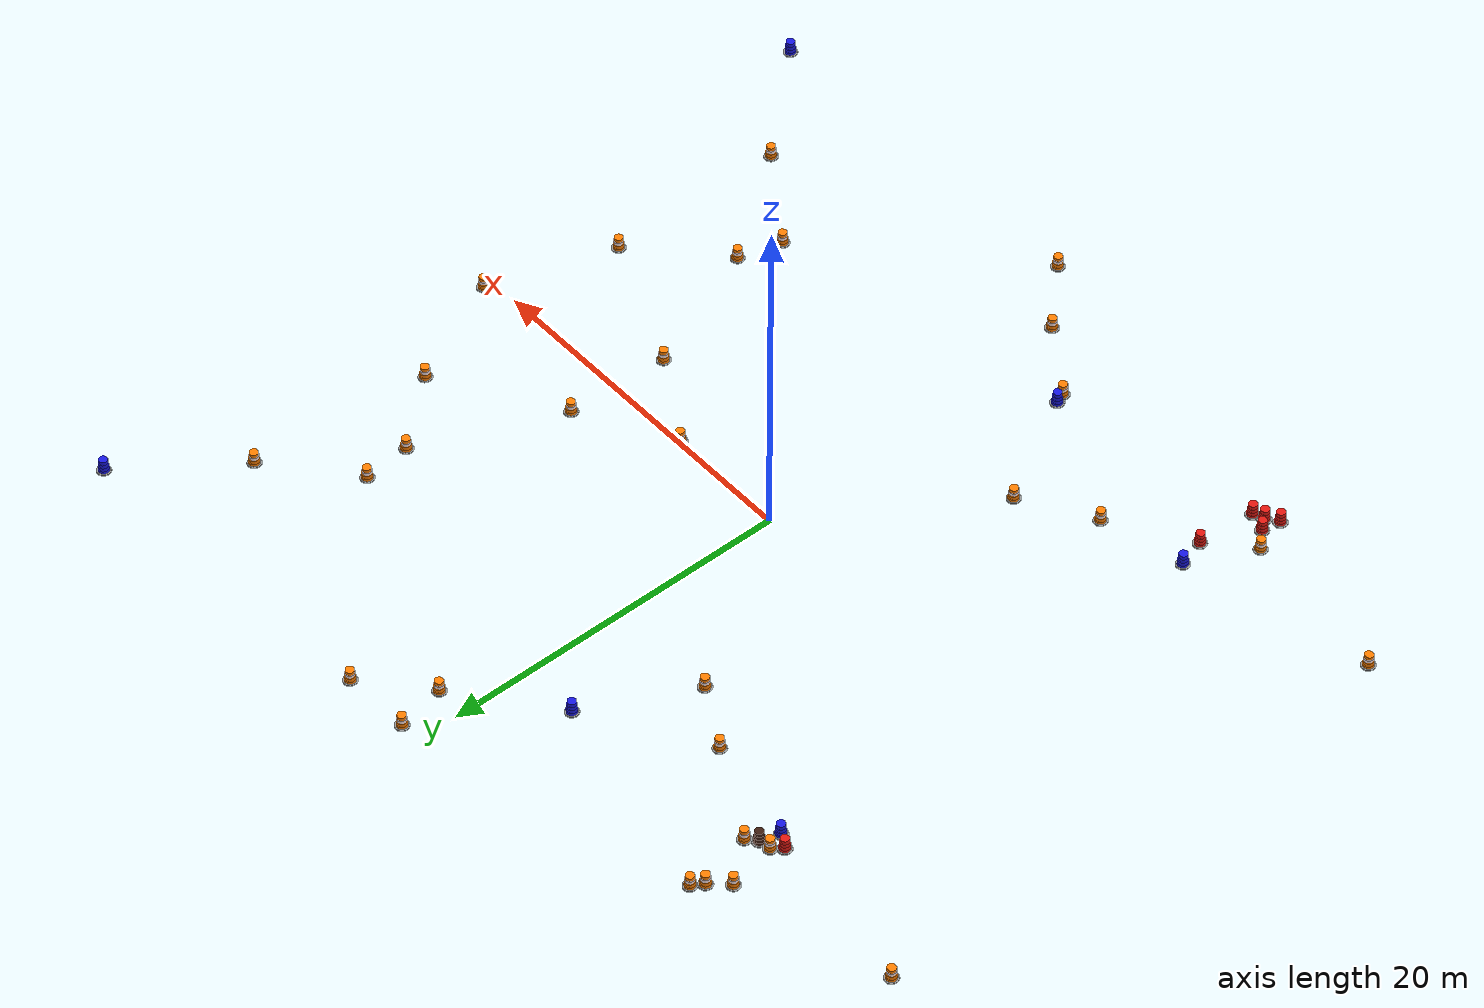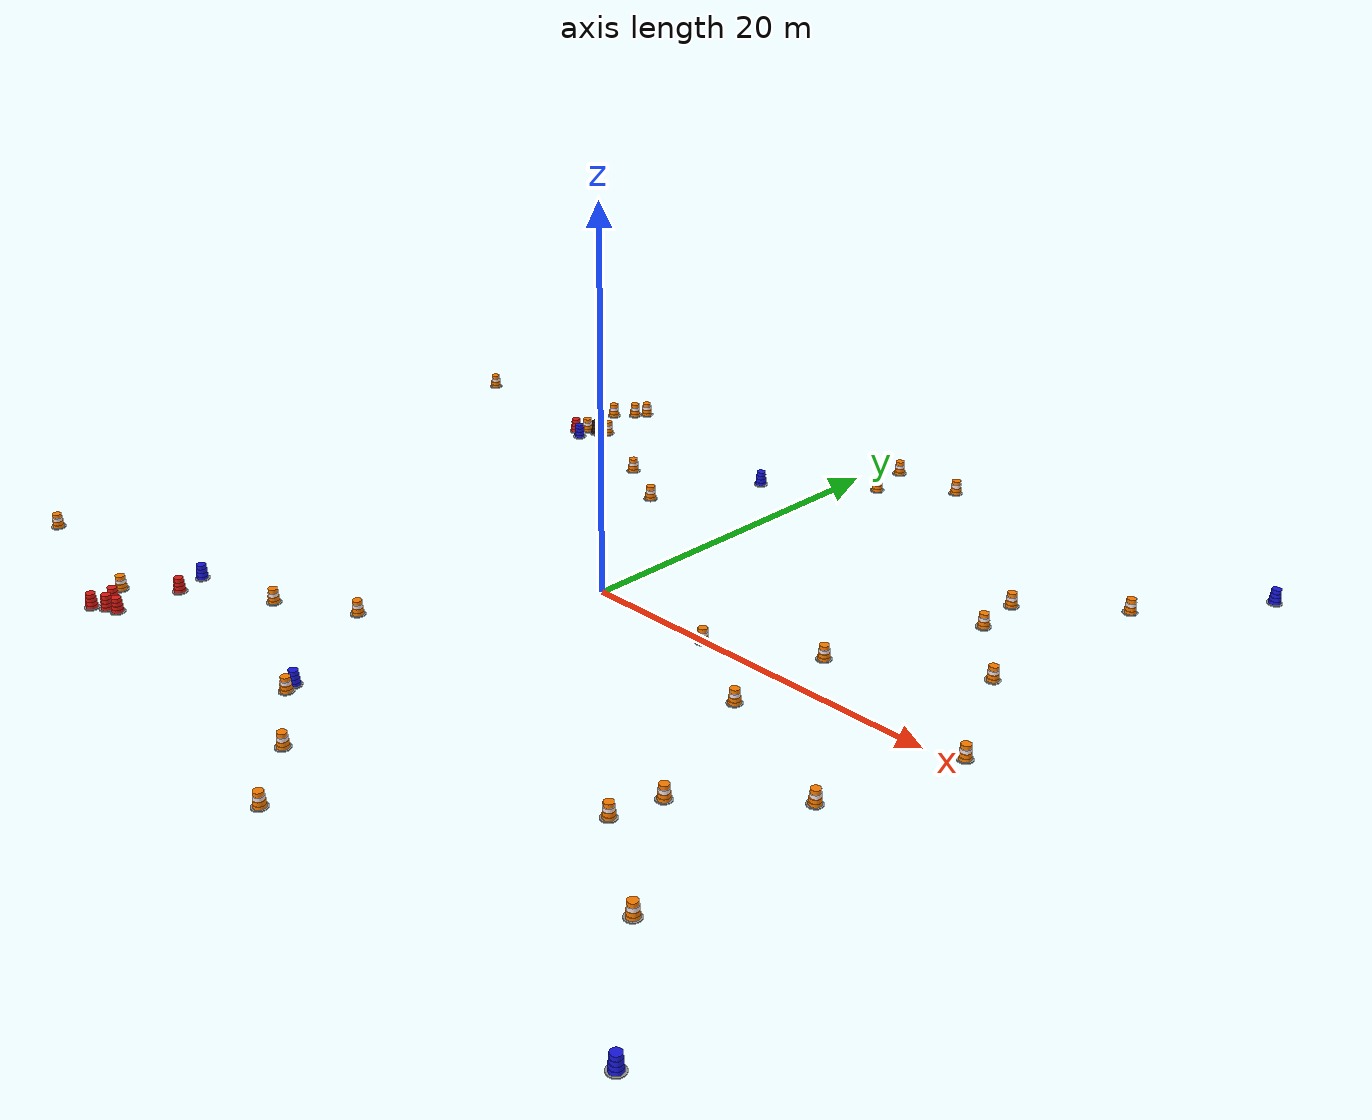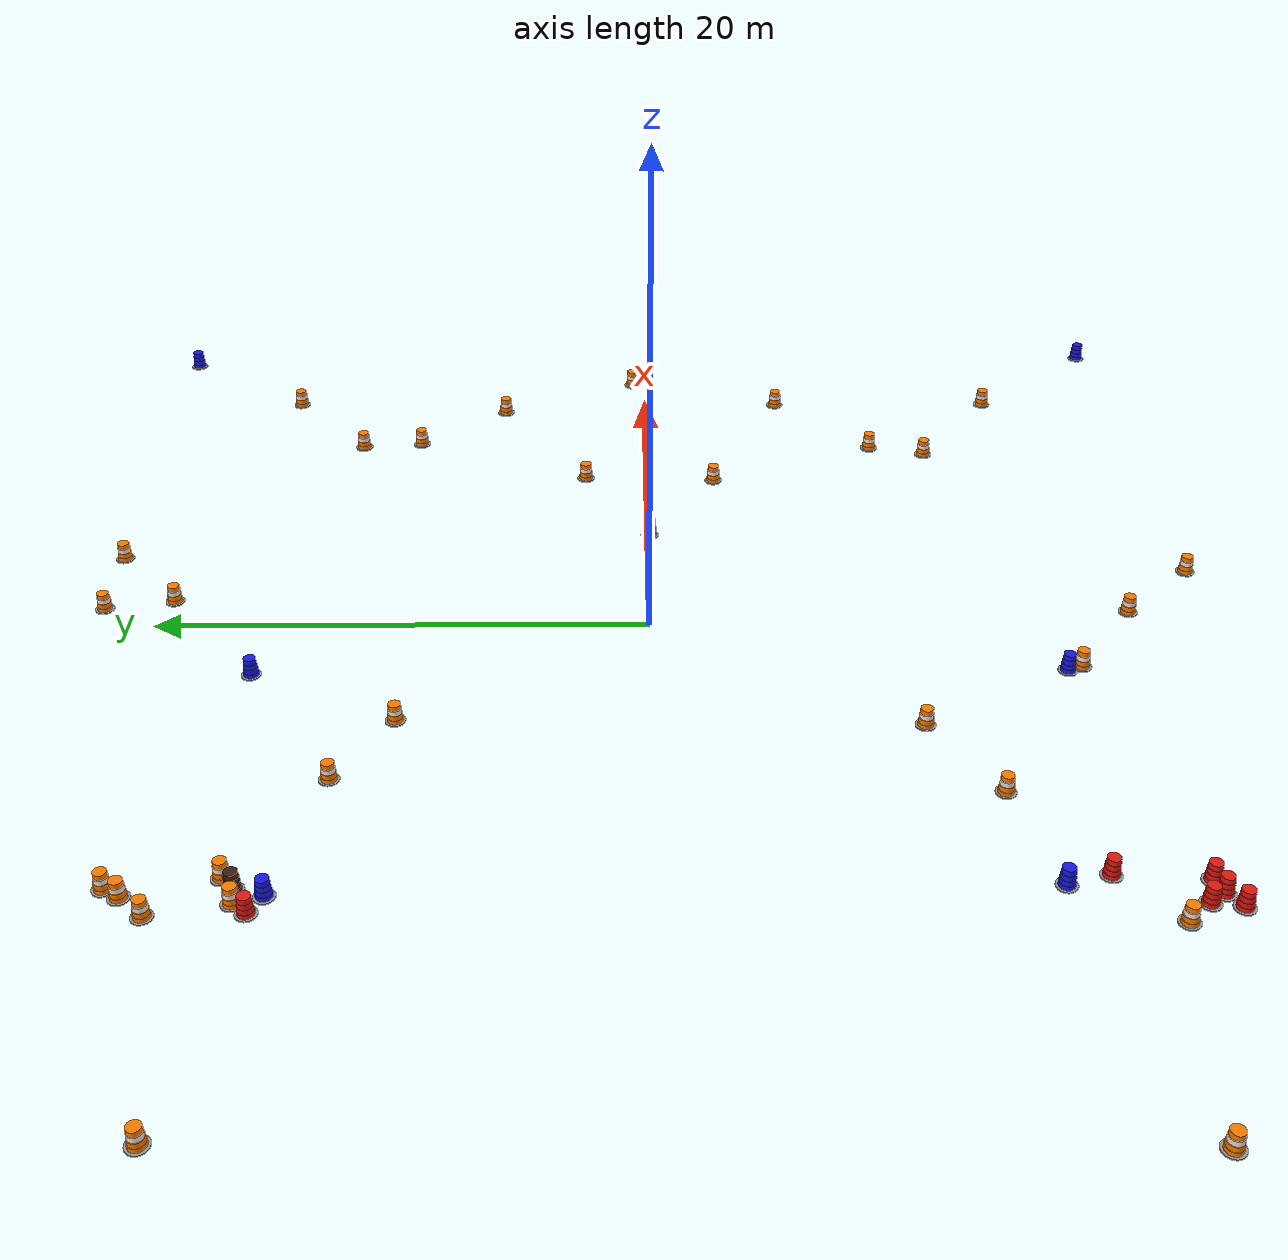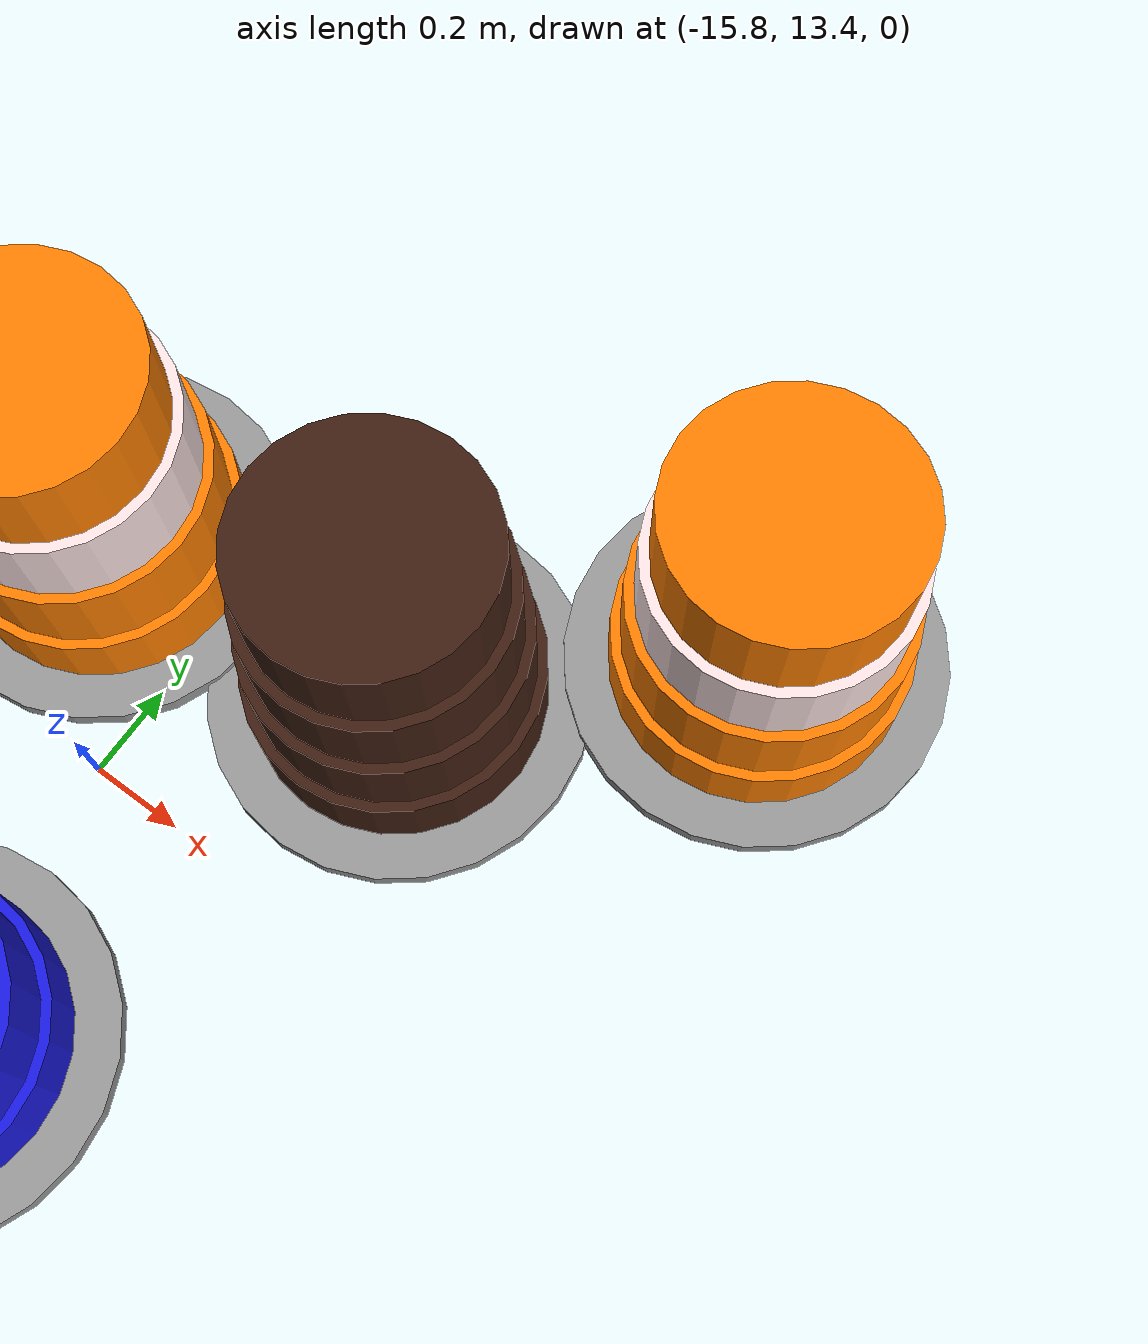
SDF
<sdf version="1.6">
 <world name="igvc_pop">
  <gravity>0 0 -9.8</gravity>
  <magnetic_field>6e-06 2.3e-05 -4.2e-05</magnetic_field>
  <atmosphere type="adiabatic"/>
  <physics type="ode">
   <max_step_size>0.01</max_step_size>
   <real_time_update_rate>100</real_time_update_rate>
   <ode>
    <solver><iters>100</iters><precon_iters>0</precon_iters><sor>1.300000</sor></solver>
    <constraints>
     <cfm>0.000000</cfm>
     <erp>0.200000</erp>
     <contact_max_correcting_vel>100.000000</contact_max_correcting_vel>
     <contact_surface_layer>0.001000</contact_surface_layer>
    </constraints>
   </ode>
  </physics>
  <scene><ambient>1 1 1 1</ambient><background>0.7 0.7 0.7 1</background><shadows>1</shadows></scene>
  <spherical_coordinates>
   <surface_model>EARTH_WGS84</surface_model>
   <latitude_deg>042.729306</latitude_deg>
   <longitude_deg>-73.680906</longitude_deg>
   <elevation>0</elevation>
   <heading_deg>180</heading_deg>
  </spherical_coordinates>
  <include><uri>model://sun</uri><pose>0 0 20   0 0 0</pose></include>
  <include>
   <uri>model://construction_barrel_blue</uri>
   <name>construction_barrel_blue</name>
   <pose>-15.3597 -13.5767 0 0 -0 0</pose>
  </include>
  <include>
   <uri>model://construction_barrel_blue</uri>
   <name>construction_barrel_blue_0</name>
   <pose>-3.22518 -16.2149 0 0 -0 0</pose>
  </include>
  <include>
   <uri>model://construction_barrel_blue</uri>
   <name>construction_barrel_blue_1_clone_3</name>
   <pose>24.0719 23.0578 0 0 -0 0</pose>
  </include>
  <include>
   <uri>model://construction_barrel_blue</uri>
   <name>construction_barrel_blue_2</name>
   <pose>-3.32971 15.4561 0 0 -0 0</pose>
  </include>
  <include>
   <uri>model://construction_barrel_blue</uri>
   <name>construction_barrel_blue_3</name>
   <pose>-15.7311 12.798 0 0 -0 0</pose>
  </include>
  <include>
   <uri>model://construction_barrel_blue</uri>
   <name>construction_barrel_blue_4</name>
   <pose>24.7467 -22.5984 0 0 -0 0</pose>
  </include>
  <include>
   <uri>model://construction_barrel_brown</uri>
   <name>construction_barrel_brown</name>
   <pose>-15.4095 13.8822 0 0 -0 0</pose>
  </include>
  <include>
   <uri>model://construction_barrel_orange</uri>
   <name>construction_barrel_orange</name>
   <pose>-26.0613 -15.9331 0 0 -0 0</pose>
  </include>
  <include>
   <uri>model://construction_barrel_orange</uri>
   <name>construction_barrel_orange_0</name>
   <pose>-17.1294 -17.1551 0 0 -0 0</pose>
  </include>
  <include>
   <uri>model://construction_barrel_orange</uri>
   <name>construction_barrel_orange_1</name>
   <pose>-10.5847 -12.4459 0 0 -0 0</pose>
  </include>
  <include>
   <uri>model://construction_barrel_orange</uri>
   <name>construction_barrel_orange_10</name>
   <pose>-6.29516 9.55127 0 0 -0 0</pose>
  </include>
  <include>
   <uri>model://construction_barrel_orange</uri>
   <name>construction_barrel_orange_10_clone</name>
   <pose>-9.73601 11.5329 0 0 -0 0</pose>
  </include>
  <include>
   <uri>model://construction_barrel_orange</uri>
   <name>construction_barrel_orange_10_clone_0</name>
   <pose>-15.378 18.1568 0 0 -0 0</pose>
  </include>
  <include>
   <uri>model://construction_barrel_orange</uri>
   <name>construction_barrel_orange_10_clone_1</name>
   <pose>-15.7902 17.5407 0 0 -0 0</pose>
  </include>
  <include>
   <uri>model://construction_barrel_orange</uri>
   <name>construction_barrel_orange_10_clone_2</name>
   <pose>-16.6827 16.5739 0 0 -0 0</pose>
  </include>
  <include>
   <uri>model://construction_barrel_orange</uri>
   <name>construction_barrel_orange_10_clone_3</name>
   <pose>-14.8633 14.3497 0 0 -0 0</pose>
  </include>
  <include>
   <uri>model://construction_barrel_orange</uri>
   <name>construction_barrel_orange_10_clone_4</name>
   <pose>-16.0925 13.7873 0 0 -0 0</pose>
  </include>
  <include>
   <uri>model://construction_barrel_orange</uri>
   <name>construction_barrel_orange_11</name>
   <pose>-25.7487 14.5841 0 0 -0 0</pose>
  </include>
  <include>
   <uri>model://construction_barrel_orange</uri>
   <name>construction_barrel_orange_12</name>
   <pose>6.99857 -0.081065 0 0 -0 0</pose>
  </include>
  <include>
   <uri>model://construction_barrel_orange</uri>
   <name>construction_barrel_orange_2</name>
   <pose>-6.68686 -10.1762 0 0 -0 0</pose>
  </include>
  <include>
   <uri>model://construction_barrel_orange</uri>
   <name>construction_barrel_orange_3</name>
   <pose>-2.98335 -16.8021 0 0 -0 0</pose>
  </include>
  <include>
   <uri>model://construction_barrel_orange</uri>
   <name>construction_barrel_orange_4</name>
   <pose>0.818162 -19.5199 0 0 -0 0</pose>
  </include>
  <include>
   <uri>model://construction_barrel_orange</uri>
   <name>construction_barrel_orange_5</name>
   <pose>3.875 -22.6825 0 0 -0 0</pose>
  </include>
  <include>
   <uri>model://construction_barrel_orange</uri>
   <name>construction_barrel_orange_6</name>
   <pose>14.9328 -10.5856 0 0 -0 0</pose>
  </include>
  <include>
   <uri>model://construction_barrel_orange</uri>
   <name>construction_barrel_orange_7</name>
   <pose>14.2893 -13.0694 0 0 -0 0</pose>
  </include>
  <include>
   <uri>model://construction_barrel_orange</uri>
   <name>construction_barrel_orange_8</name>
   <pose>19.4672 -16.7316 0 0 -0 0</pose>
  </include>
  <include>
   <uri>model://construction_barrel_orange</uri>
   <name>construction_barrel_orange_9_clone_4_clone</name>
   <pose>19.4485 -6.43545 0 0 -0 0</pose>
  </include>
  <include>
   <uri>model://construction_barrel_orange</uri>
   <name>construction_barrel_orange_9_clone_4_clone_0</name>
   <pose>11.8429 -3.06111 0 0 -0 0</pose>
  </include>
  <include>
   <uri>model://construction_barrel_orange</uri>
   <name>construction_barrel_orange_9_clone_4_clone_1</name>
   <pose>12.0898 2.79341 0 0 -0 0</pose>
  </include>
  <include>
   <uri>model://construction_barrel_orange</uri>
   <name>construction_barrel_orange_9_clone_4_clone_2</name>
   <pose>18.7139 6.84977 0 0 -0 0</pose>
  </include>
  <include>
   <uri>model://construction_barrel_orange</uri>
   <name>construction_barrel_orange_9_clone_4_clone_2_clone</name>
   <pose>19.6109 17.0436 0 0 -0 0</pose>
  </include>
  <include>
   <uri>model://construction_barrel_orange</uri>
   <name>construction_barrel_orange_9_clone_4_clone_2_clone_0</name>
   <pose>15.1681 13.3941 0 0 -0 0</pose>
  </include>
  <include>
   <uri>model://construction_barrel_orange</uri>
   <name>construction_barrel_orange_9_clone_4_clone_2_clone_1</name>
   <pose>15.4562 10.675 0 0 -0 0</pose>
  </include>
  <include>
   <uri>model://construction_barrel_orange</uri>
   <name>construction_barrel_orange_9_clone_4_clone_2_clone_2</name>
   <pose>5.18677 22.3609 0 0 -0 0</pose>
  </include>
  <include>
   <uri>model://construction_barrel_orange</uri>
   <name>construction_barrel_orange_9_clone_4_clone_2_clone_3</name>
   <pose>1.84323 19.5101 0 0 -0 0</pose>
  </include>
  <include>
   <uri>model://construction_barrel_orange</uri>
   <name>construction_barrel_orange_9_clone_4_clone_2_clone_4</name>
   <pose>1.29207 22.2602 0 0 -0 0</pose>
  </include>
  <include>
   <uri>model://construction_barrel_orange</uri>
   <name>construction_barrel_orange_9_clone_5</name>
   <pose>21.7249 0.621743 0 0 -0 0</pose>
  </include>
  <include>
   <uri>model://construction_barrel_red</uri>
   <name>construction_barrel_red</name>
   <pose>-16.2464 -18.0797 0 0 -0 0</pose>
  </include>
  <include>
   <uri>model://construction_barrel_red</uri>
   <name>construction_barrel_red_0</name>
   <pose>-15.1488 -18.4582 0 0 -0 0</pose>
  </include>
  <include>
   <uri>model://construction_barrel_red</uri>
   <name>construction_barrel_red_1</name>
   <pose>-15.7831 -18.6777 0 0 -0 0</pose>
  </include>
  <include>
   <uri>model://construction_barrel_red</uri>
   <name>construction_barrel_red_10</name>
   <pose>-16.5441 13.2465 0 0 -0 0</pose>
  </include>
  <include>
   <uri>model://construction_barrel_red</uri>
   <name>construction_barrel_red_2</name>
   <pose>-16.4394 -19.146 0 0 -0 0</pose>
  </include>
  <include>
   <uri>model://construction_barrel_red</uri>
   <name>construction_barrel_red_3</name>
   <pose>-14.8865 -15.1605 0 0 -0 0</pose>
  </include>
  <plugin name="FixFrictionNode" filename="libFixFrictionNode.so"/>
 </world>
</sdf>

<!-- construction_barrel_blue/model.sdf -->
<sdf version='1.6'>
  <model name='construction_barrel_blue'>
    <link name='link_0'>
      <pose frame=''>0 0 0.005 0 -0 0</pose>
      <inertial>
        <mass>1</mass>
        <inertia>
          <ixx>0.145833</ixx>
          <ixy>0</ixy>
          <ixz>0</ixz>
          <iyy>0.145833</iyy>
          <iyz>0</iyz>
          <izz>0.125</izz>
        </inertia>
        <pose frame=''>0 0 0 0 -0 0</pose>
      </inertial>
      <gravity>1</gravity>
      <self_collide>0</self_collide>
      <kinematic>0</kinematic>
      <visual name='visual'>
        <pose frame=''>0 0 0 0 -0 0</pose>
        <geometry>
          <cylinder>
            <radius>0.39</radius>
            <length>0.04</length>
          </cylinder>
        </geometry>
        <material>
          <lighting>1</lighting>
          <script>
            <uri>file://media/materials/scripts/gazebo.material</uri>
            <name>Gazebo/Grey</name>
          </script>
          <shader type='pixel'>
            <normal_map>__default__</normal_map>
          </shader>
          <ambient>0.3 0.3 0.3 1</ambient>
          <diffuse>0.7 0.7 0.7 1</diffuse>
          <specular>0.01 0.01 0.01 1</specular>
          <emissive>0 0 0 1</emissive>
        </material>
        <transparency>0</transparency>
        <cast_shadows>1</cast_shadows>
      </visual>
      <collision name='collision'>
        <laser_retro>0</laser_retro>
        <max_contacts>10</max_contacts>
        <pose frame=''>0 0 0 0 -0 0</pose>
        <geometry>
          <cylinder>
            <radius>0.39</radius>
            <length>0.04</length>
          </cylinder>
        </geometry>
        <surface>
          <friction>
            <ode>
              <mu>1</mu>
              <mu2>1</mu2>
              <fdir1>0 0 0</fdir1>
              <slip1>0</slip1>
              <slip2>0</slip2>
            </ode>
            <torsional>
              <coefficient>1</coefficient>
              <patch_radius>0</patch_radius>
              <surface_radius>0</surface_radius>
              <use_patch_radius>1</use_patch_radius>
              <ode>
                <slip>0</slip>
              </ode>
            </torsional>
          </friction>
          <bounce>
            <restitution_coefficient>0</restitution_coefficient>
            <threshold>1e+06</threshold>
          </bounce>
          <contact>
            <collide_without_contact>0</collide_without_contact>
            <collide_without_contact_bitmask>1</collide_without_contact_bitmask>
            <collide_bitmask>1</collide_bitmask>
            <ode>
              <soft_cfm>0</soft_cfm>
              <soft_erp>0.2</soft_erp>
              <kp>1e+13</kp>
              <kd>1</kd>
              <max_vel>0.01</max_vel>
              <min_depth>0</min_depth>
            </ode>
            <bullet>
              <split_impulse>1</split_impulse>
              <split_impulse_penetration_threshold>-0.01</split_impulse_penetration_threshold>
              <soft_cfm>0</soft_cfm>
              <soft_erp>0.2</soft_erp>
              <kp>1e+13</kp>
              <kd>1</kd>
            </bullet>
          </contact>
        </surface>
      </collision>
    </link>
    <link name='link_clone'>
      <pose frame=''>0 0 0.1 0 -0 0</pose>
      <inertial>
        <mass>0.201505</mass>
        <inertia>
          <ixx>0.0132759</ixx>
          <ixy>0</ixy>
          <ixz>0</ixz>
          <iyy>0.0132759</iyy>
          <iyz>0</iyz>
          <izz>0.0251882</izz>
        </inertia>
        <pose frame=''>0 0 0 0 -0 0</pose>
      </inertial>
      <self_collide>0</self_collide>
      <kinematic>0</kinematic>
      <gravity>1</gravity>
      <visual name='visual'>
        <geometry>
          <cylinder>
            <radius>0.3</radius>
            <length>0.2</length>
          </cylinder>
        </geometry>
        <material>
          <script>
            <name>Gazebo/Grey</name>
            <uri>file://media/materials/scripts/gazebo.material</uri>
          </script>
          <shader type='pixel'>
            <normal_map>__default__</normal_map>
          </shader>
          <ambient>0.1 0.1 0.9 1</ambient>
          <diffuse>0.1 0.1 0.9 1</diffuse>
          <specular>0.1 0.1 0.9 1</specular>
          <emissive>0 0 0 1</emissive>
        </material>
        <pose frame=''>0 0 0 0 -0 0</pose>
        <transparency>0</transparency>
        <cast_shadows>1</cast_shadows>
      </visual>
      <collision name='collision'>
        <laser_retro>0</laser_retro>
        <max_contacts>10</max_contacts>
        <pose frame=''>0 0 0 0 -0 0</pose>
        <geometry>
          <cylinder>
            <radius>0.3</radius>
            <length>0.2</length>
          </cylinder>
        </geometry>
        <surface>
          <friction>
            <ode>
              <mu>1</mu>
              <mu2>1</mu2>
              <fdir1>0 0 0</fdir1>
              <slip1>0</slip1>
              <slip2>0</slip2>
            </ode>
            <torsional>
              <coefficient>1</coefficient>
              <patch_radius>0</patch_radius>
              <surface_radius>0</surface_radius>
              <use_patch_radius>1</use_patch_radius>
              <ode>
                <slip>0</slip>
              </ode>
            </torsional>
          </friction>
          <bounce>
            <restitution_coefficient>0</restitution_coefficient>
            <threshold>1e+06</threshold>
          </bounce>
          <contact>
            <collide_without_contact>0</collide_without_contact>
            <collide_without_contact_bitmask>1</collide_without_contact_bitmask>
            <collide_bitmask>1</collide_bitmask>
            <ode>
              <soft_cfm>0</soft_cfm>
              <soft_erp>0.2</soft_erp>
              <kp>1e+13</kp>
              <kd>1</kd>
              <max_vel>0.01</max_vel>
              <min_depth>0</min_depth>
            </ode>
            <bullet>
              <split_impulse>1</split_impulse>
              <split_impulse_penetration_threshold>-0.01</split_impulse_penetration_threshold>
              <soft_cfm>0</soft_cfm>
              <soft_erp>0.2</soft_erp>
              <kp>1e+13</kp>
              <kd>1</kd>
            </bullet>
          </contact>
        </surface>
      </collision>
    </link>
    <link name='link_clone_clone'>
      <pose frame=''>0 0 0.3 0 -0 0</pose>
      <inertial>
        <mass>0.201505</mass>
        <inertia>
          <ixx>0.0132759</ixx>
          <ixy>0</ixy>
          <ixz>0</ixz>
          <iyy>0.0132759</iyy>
          <iyz>0</iyz>
          <izz>0.0251882</izz>
        </inertia>
        <pose frame=''>0 0 0 0 -0 0</pose>
      </inertial>
      <self_collide>0</self_collide>
      <kinematic>0</kinematic>
      <gravity>1</gravity>
      <visual name='visual'>
        <geometry>
          <cylinder>
            <radius>0.28</radius>
            <length>0.2</length>
          </cylinder>
        </geometry>
        <material>
          <script>
            <name>Gazebo/Grey</name>
            <uri>file://media/materials/scripts/gazebo.material</uri>
          </script>
          <shader type='pixel'>
            <normal_map>__default__</normal_map>
          </shader>
          <ambient>0.1 0.1 0.9 1</ambient>
          <diffuse>0.1 0.1 0.9 1</diffuse>
          <specular>0.1 0.1 0.9 1</specular>
          <emissive>0 0 0 1</emissive>
        </material>
        <pose frame=''>0 0 0 0 -0 0</pose>
        <transparency>0</transparency>
        <cast_shadows>1</cast_shadows>
      </visual>
      <collision name='collision'>
        <laser_retro>0</laser_retro>
        <max_contacts>10</max_contacts>
        <pose frame=''>0 0 0 0 -0 0</pose>
        <geometry>
          <cylinder>
            <radius>0.28</radius>
            <length>0.2</length>
          </cylinder>
        </geometry>
        <surface>
          <friction>
            <ode>
              <mu>1</mu>
              <mu2>1</mu2>
              <fdir1>0 0 0</fdir1>
              <slip1>0</slip1>
              <slip2>0</slip2>
            </ode>
            <torsional>
              <coefficient>1</coefficient>
              <patch_radius>0</patch_radius>
              <surface_radius>0</surface_radius>
              <use_patch_radius>1</use_patch_radius>
              <ode>
                <slip>0</slip>
              </ode>
            </torsional>
          </friction>
          <bounce>
            <restitution_coefficient>0</restitution_coefficient>
            <threshold>1e+06</threshold>
          </bounce>
          <contact>
            <collide_without_contact>0</collide_without_contact>
            <collide_without_contact_bitmask>1</collide_without_contact_bitmask>
            <collide_bitmask>1</collide_bitmask>
            <ode>
              <soft_cfm>0</soft_cfm>
              <soft_erp>0.2</soft_erp>
              <kp>1e+13</kp>
              <kd>1</kd>
              <max_vel>0.01</max_vel>
              <min_depth>0</min_depth>
            </ode>
            <bullet>
              <split_impulse>1</split_impulse>
              <split_impulse_penetration_threshold>-0.01</split_impulse_penetration_threshold>
              <soft_cfm>0</soft_cfm>
              <soft_erp>0.2</soft_erp>
              <kp>1e+13</kp>
              <kd>1</kd>
            </bullet>
          </contact>
        </surface>
      </collision>
    </link>
    <link name='link_clone_clone_0'>
      <pose frame=''>0 0 0.5 0 0 0</pose>
      <inertial>
        <mass>0.201505</mass>
        <inertia>
          <ixx>0.0132759</ixx>
          <ixy>0</ixy>
          <ixz>0</ixz>
          <iyy>0.0132759</iyy>
          <iyz>0</iyz>
          <izz>0.0251882</izz>
        </inertia>
        <pose frame=''>0 0 0 0 -0 0</pose>
      </inertial>
      <self_collide>0</self_collide>
      <kinematic>0</kinematic>
      <gravity>1</gravity>
      <visual name='visual'>
        <geometry>
          <cylinder>
            <radius>0.26</radius>
            <length>0.2</length>
          </cylinder>
        </geometry>
        <material>
          <script>
            <name>Gazebo/Grey</name>
            <uri>file://media/materials/scripts/gazebo.material</uri>
          </script>
          <shader type='pixel'>
            <normal_map>__default__</normal_map>
          </shader>
          <ambient>0.1 0.1 0.9 1</ambient>
          <diffuse>0.1 0.1 0.9 1</diffuse>
          <specular>0.1 0.1 0.9 1</specular>
          <emissive>0 0 0 1</emissive>
        </material>
        <pose frame=''>0 0 0 0 -0 0</pose>
        <transparency>0</transparency>
        <cast_shadows>1</cast_shadows>
      </visual>
      <collision name='collision'>
        <laser_retro>0</laser_retro>
        <max_contacts>10</max_contacts>
        <pose frame=''>0 0 0 0 -0 0</pose>
        <geometry>
          <cylinder>
            <radius>0.26</radius>
            <length>0.2</length>
          </cylinder>
        </geometry>
        <surface>
          <friction>
            <ode>
              <mu>1</mu>
              <mu2>1</mu2>
              <fdir1>0 0 0</fdir1>
              <slip1>0</slip1>
              <slip2>0</slip2>
            </ode>
            <torsional>
              <coefficient>1</coefficient>
              <patch_radius>0</patch_radius>
              <surface_radius>0</surface_radius>
              <use_patch_radius>1</use_patch_radius>
              <ode>
                <slip>0</slip>
              </ode>
            </torsional>
          </friction>
          <bounce>
            <restitution_coefficient>0</restitution_coefficient>
            <threshold>1e+06</threshold>
          </bounce>
          <contact>
            <collide_without_contact>0</collide_without_contact>
            <collide_without_contact_bitmask>1</collide_without_contact_bitmask>
            <collide_bitmask>1</collide_bitmask>
            <ode>
              <soft_cfm>0</soft_cfm>
              <soft_erp>0.2</soft_erp>
              <kp>1e+13</kp>
              <kd>1</kd>
              <max_vel>0.01</max_vel>
              <min_depth>0</min_depth>
            </ode>
            <bullet>
              <split_impulse>1</split_impulse>
              <split_impulse_penetration_threshold>-0.01</split_impulse_penetration_threshold>
              <soft_cfm>0</soft_cfm>
              <soft_erp>0.2</soft_erp>
              <kp>1e+13</kp>
              <kd>1</kd>
            </bullet>
          </contact>
        </surface>
      </collision>
    </link>
    <link name='link_clone_clone_1'>
      <pose frame=''>-0 -0 0.7 0 -0 0</pose>
      <inertial>
        <mass>0.201505</mass>
        <inertia>
          <ixx>0.0132759</ixx>
          <ixy>0</ixy>
          <ixz>0</ixz>
          <iyy>0.0132759</iyy>
          <iyz>0</iyz>
          <izz>0.0251882</izz>
        </inertia>
        <pose frame=''>0 0 0 0 -0 0</pose>
      </inertial>
      <self_collide>0</self_collide>
      <kinematic>0</kinematic>
      <gravity>1</gravity>
      <visual name='visual'>
        <geometry>
          <cylinder>
            <radius>0.24</radius>
            <length>0.2</length>
          </cylinder>
        </geometry>
        <material>
          <script>
            <name>Gazebo/Grey</name>
            <uri>file://media/materials/scripts/gazebo.material</uri>
          </script>
          <shader type='pixel'>
            <normal_map>__default__</normal_map>
          </shader>
          <ambient>0.1 0.1 0.9 1</ambient>
          <diffuse>0.1 0.1 0.9 1</diffuse>
          <specular>0.1 0.1 0.9 1</specular>
          <emissive>0 0 0 1</emissive>
        </material>
        <pose frame=''>0 0 0 0 -0 0</pose>
        <transparency>0</transparency>
        <cast_shadows>1</cast_shadows>
      </visual>
      <collision name='collision'>
        <laser_retro>0</laser_retro>
        <max_contacts>10</max_contacts>
        <pose frame=''>0 0 0 0 -0 0</pose>
        <geometry>
          <cylinder>
            <radius>0.24</radius>
            <length>0.2</length>
          </cylinder>
        </geometry>
        <surface>
          <friction>
            <ode>
              <mu>1</mu>
              <mu2>1</mu2>
              <fdir1>0 0 0</fdir1>
              <slip1>0</slip1>
              <slip2>0</slip2>
            </ode>
            <torsional>
              <coefficient>1</coefficient>
              <patch_radius>0</patch_radius>
              <surface_radius>0</surface_radius>
              <use_patch_radius>1</use_patch_radius>
              <ode>
                <slip>0</slip>
              </ode>
            </torsional>
          </friction>
          <bounce>
            <restitution_coefficient>0</restitution_coefficient>
            <threshold>1e+06</threshold>
          </bounce>
          <contact>
            <collide_without_contact>0</collide_without_contact>
            <collide_without_contact_bitmask>1</collide_without_contact_bitmask>
            <collide_bitmask>1</collide_bitmask>
            <ode>
              <soft_cfm>0</soft_cfm>
              <soft_erp>0.2</soft_erp>
              <kp>1e+13</kp>
              <kd>1</kd>
              <max_vel>0.01</max_vel>
              <min_depth>0</min_depth>
            </ode>
            <bullet>
              <split_impulse>1</split_impulse>
              <split_impulse_penetration_threshold>-0.01</split_impulse_penetration_threshold>
              <soft_cfm>0</soft_cfm>
              <soft_erp>0.2</soft_erp>
              <kp>1e+13</kp>
              <kd>1</kd>
            </bullet>
          </contact>
        </surface>
      </collision>
    </link>
    <static>1</static>
    <allow_auto_disable>1</allow_auto_disable>
  </model>
</sdf>

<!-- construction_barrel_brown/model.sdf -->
<sdf version='1.6'>
  <model name='construction_barrel_brown'>
    <link name='link_0'>
      <pose frame=''>0 0 0.005 0 -0 0</pose>
      <inertial>
        <mass>1</mass>
        <inertia>
          <ixx>0.145833</ixx>
          <ixy>0</ixy>
          <ixz>0</ixz>
          <iyy>0.145833</iyy>
          <iyz>0</iyz>
          <izz>0.125</izz>
        </inertia>
        <pose frame=''>0 0 0 0 -0 0</pose>
      </inertial>
      <gravity>1</gravity>
      <self_collide>0</self_collide>
      <kinematic>0</kinematic>
      <visual name='visual'>
        <pose frame=''>0 0 0 0 -0 0</pose>
        <geometry>
          <cylinder>
            <radius>0.39</radius>
            <length>0.04</length>
          </cylinder>
        </geometry>
        <material>
          <lighting>1</lighting>
          <script>
            <uri>file://media/materials/scripts/gazebo.material</uri>
            <name>Gazebo/Grey</name>
          </script>
          <shader type='pixel'>
            <normal_map>__default__</normal_map>
          </shader>
          <ambient>0.3 0.3 0.3 1</ambient>
          <diffuse>0.7 0.7 0.7 1</diffuse>
          <specular>0.01 0.01 0.01 1</specular>
          <emissive>0 0 0 1</emissive>
        </material>
        <transparency>0</transparency>
        <cast_shadows>1</cast_shadows>
      </visual>
      <collision name='collision'>
        <laser_retro>0</laser_retro>
        <max_contacts>10</max_contacts>
        <pose frame=''>0 0 0 0 -0 0</pose>
        <geometry>
          <cylinder>
            <radius>0.39</radius>
            <length>0.04</length>
          </cylinder>
        </geometry>
        <surface>
          <friction>
            <ode>
              <mu>1</mu>
              <mu2>1</mu2>
              <fdir1>0 0 0</fdir1>
              <slip1>0</slip1>
              <slip2>0</slip2>
            </ode>
            <torsional>
              <coefficient>1</coefficient>
              <patch_radius>0</patch_radius>
              <surface_radius>0</surface_radius>
              <use_patch_radius>1</use_patch_radius>
              <ode>
                <slip>0</slip>
              </ode>
            </torsional>
          </friction>
          <bounce>
            <restitution_coefficient>0</restitution_coefficient>
            <threshold>1e+06</threshold>
          </bounce>
          <contact>
            <collide_without_contact>0</collide_without_contact>
            <collide_without_contact_bitmask>1</collide_without_contact_bitmask>
            <collide_bitmask>1</collide_bitmask>
            <ode>
              <soft_cfm>0</soft_cfm>
              <soft_erp>0.2</soft_erp>
              <kp>1e+13</kp>
              <kd>1</kd>
              <max_vel>0.01</max_vel>
              <min_depth>0</min_depth>
            </ode>
            <bullet>
              <split_impulse>1</split_impulse>
              <split_impulse_penetration_threshold>-0.01</split_impulse_penetration_threshold>
              <soft_cfm>0</soft_cfm>
              <soft_erp>0.2</soft_erp>
              <kp>1e+13</kp>
              <kd>1</kd>
            </bullet>
          </contact>
        </surface>
      </collision>
    </link>
    <link name='link_clone'>
      <pose frame=''>0 0 0.1 0 -0 0</pose>
      <inertial>
        <mass>0.201505</mass>
        <inertia>
          <ixx>0.0132759</ixx>
          <ixy>0</ixy>
          <ixz>0</ixz>
          <iyy>0.0132759</iyy>
          <iyz>0</iyz>
          <izz>0.0251882</izz>
        </inertia>
        <pose frame=''>0 0 0 0 -0 0</pose>
      </inertial>
      <self_collide>0</self_collide>
      <kinematic>0</kinematic>
      <gravity>1</gravity>
      <visual name='visual'>
        <geometry>
          <cylinder>
            <radius>0.3</radius>
            <length>0.2</length>
          </cylinder>
        </geometry>
        <material>
          <script>
            <name>Gazebo/Grey</name>
            <uri>file://media/materials/scripts/gazebo.material</uri>
          </script>
          <shader type='pixel'>
            <normal_map>__default__</normal_map>
          </shader>
          <ambient>0.25 0.12 0.07 1</ambient>
          <diffuse>0.25 0.12 0.07 1</diffuse>
          <specular>0.25 0.12 0.07 1</specular>
          <emissive>0 0 0 1</emissive>
        </material>
        <pose frame=''>0 0 0 0 -0 0</pose>
        <transparency>0</transparency>
        <cast_shadows>1</cast_shadows>
      </visual>
      <collision name='collision'>
        <laser_retro>0</laser_retro>
        <max_contacts>10</max_contacts>
        <pose frame=''>0 0 0 0 -0 0</pose>
        <geometry>
          <cylinder>
            <radius>0.3</radius>
            <length>0.2</length>
          </cylinder>
        </geometry>
        <surface>
          <friction>
            <ode>
              <mu>1</mu>
              <mu2>1</mu2>
              <fdir1>0 0 0</fdir1>
              <slip1>0</slip1>
              <slip2>0</slip2>
            </ode>
            <torsional>
              <coefficient>1</coefficient>
              <patch_radius>0</patch_radius>
              <surface_radius>0</surface_radius>
              <use_patch_radius>1</use_patch_radius>
              <ode>
                <slip>0</slip>
              </ode>
            </torsional>
          </friction>
          <bounce>
            <restitution_coefficient>0</restitution_coefficient>
            <threshold>1e+06</threshold>
          </bounce>
          <contact>
            <collide_without_contact>0</collide_without_contact>
            <collide_without_contact_bitmask>1</collide_without_contact_bitmask>
            <collide_bitmask>1</collide_bitmask>
            <ode>
              <soft_cfm>0</soft_cfm>
              <soft_erp>0.2</soft_erp>
              <kp>1e+13</kp>
              <kd>1</kd>
              <max_vel>0.01</max_vel>
              <min_depth>0</min_depth>
            </ode>
            <bullet>
              <split_impulse>1</split_impulse>
              <split_impulse_penetration_threshold>-0.01</split_impulse_penetration_threshold>
              <soft_cfm>0</soft_cfm>
              <soft_erp>0.2</soft_erp>
              <kp>1e+13</kp>
              <kd>1</kd>
            </bullet>
          </contact>
        </surface>
      </collision>
    </link>
    <link name='link_clone_clone'>
      <pose frame=''>0 0 0.3 0 -0 0</pose>
      <inertial>
        <mass>0.201505</mass>
        <inertia>
          <ixx>0.0132759</ixx>
          <ixy>0</ixy>
          <ixz>0</ixz>
          <iyy>0.0132759</iyy>
          <iyz>0</iyz>
          <izz>0.0251882</izz>
        </inertia>
        <pose frame=''>0 0 0 0 -0 0</pose>
      </inertial>
      <self_collide>0</self_collide>
      <kinematic>0</kinematic>
      <gravity>1</gravity>
      <visual name='visual'>
        <geometry>
          <cylinder>
            <radius>0.28</radius>
            <length>0.2</length>
          </cylinder>
        </geometry>
        <material>
          <script>
            <name>Gazebo/Grey</name>
            <uri>file://media/materials/scripts/gazebo.material</uri>
          </script>
          <shader type='pixel'>
            <normal_map>__default__</normal_map>
          </shader>
          <ambient>0.25 0.12 0.07 1</ambient>
          <diffuse>0.25 0.12 0.07 1</diffuse>
          <specular>0.25 0.12 0.07 1</specular>
          <emissive>0 0 0 1</emissive>
        </material>
        <pose frame=''>0 0 0 0 -0 0</pose>
        <transparency>0</transparency>
        <cast_shadows>1</cast_shadows>
      </visual>
      <collision name='collision'>
        <laser_retro>0</laser_retro>
        <max_contacts>10</max_contacts>
        <pose frame=''>0 0 0 0 -0 0</pose>
        <geometry>
          <cylinder>
            <radius>0.28</radius>
            <length>0.2</length>
          </cylinder>
        </geometry>
        <surface>
          <friction>
            <ode>
              <mu>1</mu>
              <mu2>1</mu2>
              <fdir1>0 0 0</fdir1>
              <slip1>0</slip1>
              <slip2>0</slip2>
            </ode>
            <torsional>
              <coefficient>1</coefficient>
              <patch_radius>0</patch_radius>
              <surface_radius>0</surface_radius>
              <use_patch_radius>1</use_patch_radius>
              <ode>
                <slip>0</slip>
              </ode>
            </torsional>
          </friction>
          <bounce>
            <restitution_coefficient>0</restitution_coefficient>
            <threshold>1e+06</threshold>
          </bounce>
          <contact>
            <collide_without_contact>0</collide_without_contact>
            <collide_without_contact_bitmask>1</collide_without_contact_bitmask>
            <collide_bitmask>1</collide_bitmask>
            <ode>
              <soft_cfm>0</soft_cfm>
              <soft_erp>0.2</soft_erp>
              <kp>1e+13</kp>
              <kd>1</kd>
              <max_vel>0.01</max_vel>
              <min_depth>0</min_depth>
            </ode>
            <bullet>
              <split_impulse>1</split_impulse>
              <split_impulse_penetration_threshold>-0.01</split_impulse_penetration_threshold>
              <soft_cfm>0</soft_cfm>
              <soft_erp>0.2</soft_erp>
              <kp>1e+13</kp>
              <kd>1</kd>
            </bullet>
          </contact>
        </surface>
      </collision>
    </link>
    <link name='link_clone_clone_0'>
      <pose frame=''>0 0 0.5 0 0 0</pose>
      <inertial>
        <mass>0.201505</mass>
        <inertia>
          <ixx>0.0132759</ixx>
          <ixy>0</ixy>
          <ixz>0</ixz>
          <iyy>0.0132759</iyy>
          <iyz>0</iyz>
          <izz>0.0251882</izz>
        </inertia>
        <pose frame=''>0 0 0 0 -0 0</pose>
      </inertial>
      <self_collide>0</self_collide>
      <kinematic>0</kinematic>
      <gravity>1</gravity>
      <visual name='visual'>
        <geometry>
          <cylinder>
            <radius>0.26</radius>
            <length>0.2</length>
          </cylinder>
        </geometry>
        <material>
          <script>
            <name>Gazebo/Grey</name>
            <uri>file://media/materials/scripts/gazebo.material</uri>
          </script>
          <shader type='pixel'>
            <normal_map>__default__</normal_map>
          </shader>
          <ambient>0.25 0.12 0.07 1</ambient>
          <diffuse>0.25 0.12 0.07 1</diffuse>
          <specular>0.25 0.12 0.07 1</specular>
          <emissive>0 0 0 1</emissive>
        </material>
        <pose frame=''>0 0 0 0 -0 0</pose>
        <transparency>0</transparency>
        <cast_shadows>1</cast_shadows>
      </visual>
      <collision name='collision'>
        <laser_retro>0</laser_retro>
        <max_contacts>10</max_contacts>
        <pose frame=''>0 0 0 0 -0 0</pose>
        <geometry>
          <cylinder>
            <radius>0.26</radius>
            <length>0.2</length>
          </cylinder>
        </geometry>
        <surface>
          <friction>
            <ode>
              <mu>1</mu>
              <mu2>1</mu2>
              <fdir1>0 0 0</fdir1>
              <slip1>0</slip1>
              <slip2>0</slip2>
            </ode>
            <torsional>
              <coefficient>1</coefficient>
              <patch_radius>0</patch_radius>
              <surface_radius>0</surface_radius>
              <use_patch_radius>1</use_patch_radius>
              <ode>
                <slip>0</slip>
              </ode>
            </torsional>
          </friction>
          <bounce>
            <restitution_coefficient>0</restitution_coefficient>
            <threshold>1e+06</threshold>
          </bounce>
          <contact>
            <collide_without_contact>0</collide_without_contact>
            <collide_without_contact_bitmask>1</collide_without_contact_bitmask>
            <collide_bitmask>1</collide_bitmask>
            <ode>
              <soft_cfm>0</soft_cfm>
              <soft_erp>0.2</soft_erp>
              <kp>1e+13</kp>
              <kd>1</kd>
              <max_vel>0.01</max_vel>
              <min_depth>0</min_depth>
            </ode>
            <bullet>
              <split_impulse>1</split_impulse>
              <split_impulse_penetration_threshold>-0.01</split_impulse_penetration_threshold>
              <soft_cfm>0</soft_cfm>
              <soft_erp>0.2</soft_erp>
              <kp>1e+13</kp>
              <kd>1</kd>
            </bullet>
          </contact>
        </surface>
      </collision>
    </link>
    <link name='link_clone_clone_1'>
      <pose frame=''>-0 -0 0.7 0 -0 0</pose>
      <inertial>
        <mass>0.201505</mass>
        <inertia>
          <ixx>0.0132759</ixx>
          <ixy>0</ixy>
          <ixz>0</ixz>
          <iyy>0.0132759</iyy>
          <iyz>0</iyz>
          <izz>0.0251882</izz>
        </inertia>
        <pose frame=''>0 0 0 0 -0 0</pose>
      </inertial>
      <self_collide>0</self_collide>
      <kinematic>0</kinematic>
      <gravity>1</gravity>
      <visual name='visual'>
        <geometry>
          <cylinder>
            <radius>0.24</radius>
            <length>0.2</length>
          </cylinder>
        </geometry>
        <material>
          <script>
            <name>Gazebo/Grey</name>
            <uri>file://media/materials/scripts/gazebo.material</uri>
          </script>
          <shader type='pixel'>
            <normal_map>__default__</normal_map>
          </shader>
          <ambient>0.25 0.12 0.07 1</ambient>
          <diffuse>0.25 0.12 0.07 1</diffuse>
          <specular>0.25 0.12 0.07 1</specular>
          <emissive>0 0 0 1</emissive>
        </material>
        <pose frame=''>0 0 0 0 -0 0</pose>
        <transparency>0</transparency>
        <cast_shadows>1</cast_shadows>
      </visual>
      <collision name='collision'>
        <laser_retro>0</laser_retro>
        <max_contacts>10</max_contacts>
        <pose frame=''>0 0 0 0 -0 0</pose>
        <geometry>
          <cylinder>
            <radius>0.24</radius>
            <length>0.2</length>
          </cylinder>
        </geometry>
        <surface>
          <friction>
            <ode>
              <mu>1</mu>
              <mu2>1</mu2>
              <fdir1>0 0 0</fdir1>
              <slip1>0</slip1>
              <slip2>0</slip2>
            </ode>
            <torsional>
              <coefficient>1</coefficient>
              <patch_radius>0</patch_radius>
              <surface_radius>0</surface_radius>
              <use_patch_radius>1</use_patch_radius>
              <ode>
                <slip>0</slip>
              </ode>
            </torsional>
          </friction>
          <bounce>
            <restitution_coefficient>0</restitution_coefficient>
            <threshold>1e+06</threshold>
          </bounce>
          <contact>
            <collide_without_contact>0</collide_without_contact>
            <collide_without_contact_bitmask>1</collide_without_contact_bitmask>
            <collide_bitmask>1</collide_bitmask>
            <ode>
              <soft_cfm>0</soft_cfm>
              <soft_erp>0.2</soft_erp>
              <kp>1e+13</kp>
              <kd>1</kd>
              <max_vel>0.01</max_vel>
              <min_depth>0</min_depth>
            </ode>
            <bullet>
              <split_impulse>1</split_impulse>
              <split_impulse_penetration_threshold>-0.01</split_impulse_penetration_threshold>
              <soft_cfm>0</soft_cfm>
              <soft_erp>0.2</soft_erp>
              <kp>1e+13</kp>
              <kd>1</kd>
            </bullet>
          </contact>
        </surface>
      </collision>
    </link>
    <static>1</static>
    <allow_auto_disable>1</allow_auto_disable>
  </model>
</sdf>

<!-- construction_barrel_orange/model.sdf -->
<sdf version='1.6'>
  <model name='construction_barrel_orange'>
    <link name='rubber_skirt'>
      <pose frame=''>0 0 0.02 0 -0 0</pose>
      <inertial>
        <mass>1</mass>
        <inertia>
          <ixx>0.145833</ixx>
          <ixy>0</ixy>
          <ixz>0</ixz>
          <iyy>0.145833</iyy>
          <iyz>0</iyz>
          <izz>0.125</izz>
        </inertia>
        <pose frame=''>0 0 0 0 -0 0</pose>
      </inertial>
      <self_collide>0</self_collide>
      <kinematic>0</kinematic>
      <visual name='visual'>
        <pose frame=''>0 0 0 0 -0 0</pose>
        <geometry>
          <cylinder>
            <radius>0.39</radius>
            <length>0.04</length>
          </cylinder>
        </geometry>
        <material>
          <lighting>1</lighting>
          <script>
            <uri>file://media/materials/scripts/gazebo.material</uri>
            <name>Gazebo/Grey</name>
          </script>
          <shader type='pixel'>
            <normal_map>__default__</normal_map>
          </shader>
          <ambient>0.3 0.3 0.3 1</ambient>
          <diffuse>0.7 0.7 0.7 1</diffuse>
          <specular>0.01 0.01 0.01 1</specular>
          <emissive>0 0 0 1</emissive>
        </material>
        <transparency>0</transparency>
        <cast_shadows>1</cast_shadows>
      </visual>
      <collision name='collision'>
        <laser_retro>0</laser_retro>
        <max_contacts>10</max_contacts>
        <pose frame=''>0 0 0 0 -0 0</pose>
        <geometry>
          <cylinder>
            <radius>0.39</radius>
            <length>0.04</length>
          </cylinder>
        </geometry>
        <surface>
          <friction>
            <ode>
              <mu>1</mu>
              <mu2>1</mu2>
              <fdir1>0 0 0</fdir1>
              <slip1>0</slip1>
              <slip2>0</slip2>
            </ode>
            <torsional>
              <coefficient>1</coefficient>
              <patch_radius>0</patch_radius>
              <surface_radius>0</surface_radius>
              <use_patch_radius>1</use_patch_radius>
              <ode>
                <slip>0</slip>
              </ode>
            </torsional>
          </friction>
          <bounce>
            <restitution_coefficient>0</restitution_coefficient>
            <threshold>1e+06</threshold>
          </bounce>
          <contact>
            <collide_without_contact>0</collide_without_contact>
            <collide_without_contact_bitmask>1</collide_without_contact_bitmask>
            <collide_bitmask>1</collide_bitmask>
            <ode>
              <soft_cfm>0</soft_cfm>
              <soft_erp>0.2</soft_erp>
              <kp>1e+13</kp>
              <kd>1</kd>
              <max_vel>0.01</max_vel>
              <min_depth>0</min_depth>
            </ode>
            <bullet>
              <split_impulse>1</split_impulse>
              <split_impulse_penetration_threshold>-0.01</split_impulse_penetration_threshold>
              <soft_cfm>0</soft_cfm>
              <soft_erp>0.2</soft_erp>
              <kp>1e+13</kp>
              <kd>1</kd>
            </bullet>
          </contact>
        </surface>
      </collision>
    </link>
    <link name='drum_1'>
      <pose frame=''>0 0 0.1 0 -0 0</pose>
      <inertial>
        <mass>0.201505</mass>
        <inertia>
          <ixx>0.0132759</ixx>
          <ixy>0</ixy>
          <ixz>0</ixz>
          <iyy>0.0132759</iyy>
          <iyz>0</iyz>
          <izz>0.0251882</izz>
        </inertia>
        <pose frame=''>0 0 0 0 -0 0</pose>
      </inertial>
      <self_collide>0</self_collide>
      <kinematic>0</kinematic>
      <visual name='visual'>
        <geometry>
          <cylinder>
            <radius>0.3</radius>
            <length>0.2</length>
          </cylinder>
        </geometry>
        <material>
          <script>
            <name>Gazebo/Grey</name>
            <uri>file://media/materials/scripts/gazebo.material</uri>
          </script>
          <shader type='pixel'>
            <normal_map>__default__</normal_map>
          </shader>
          <ambient>1 0.5 0 1</ambient>
          <diffuse>1 0.5 0 1</diffuse>
          <specular>1 0.5 0 1</specular>
          <emissive>0 0 0 1</emissive>
        </material>
        <pose frame=''>0 0 0 0 -0 0</pose>
        <transparency>0</transparency>
        <cast_shadows>1</cast_shadows>
      </visual>
      <collision name='collision'>
        <laser_retro>0</laser_retro>
        <max_contacts>10</max_contacts>
        <pose frame=''>0 0 0 0 -0 0</pose>
        <geometry>
          <cylinder>
            <radius>0.3</radius>
            <length>0.2</length>
          </cylinder>
        </geometry>
        <surface>
          <friction>
            <ode>
              <mu>1</mu>
              <mu2>1</mu2>
              <fdir1>0 0 0</fdir1>
              <slip1>0</slip1>
              <slip2>0</slip2>
            </ode>
            <torsional>
              <coefficient>1</coefficient>
              <patch_radius>0</patch_radius>
              <surface_radius>0</surface_radius>
              <use_patch_radius>1</use_patch_radius>
              <ode>
                <slip>0</slip>
              </ode>
            </torsional>
          </friction>
          <bounce>
            <restitution_coefficient>0</restitution_coefficient>
            <threshold>1e+06</threshold>
          </bounce>
          <contact>
            <collide_without_contact>0</collide_without_contact>
            <collide_without_contact_bitmask>1</collide_without_contact_bitmask>
            <collide_bitmask>1</collide_bitmask>
            <ode>
              <soft_cfm>0</soft_cfm>
              <soft_erp>0.2</soft_erp>
              <kp>1e+13</kp>
              <kd>1</kd>
              <max_vel>0.01</max_vel>
              <min_depth>0</min_depth>
            </ode>
            <bullet>
              <split_impulse>1</split_impulse>
              <split_impulse_penetration_threshold>-0.01</split_impulse_penetration_threshold>
              <soft_cfm>0</soft_cfm>
              <soft_erp>0.2</soft_erp>
              <kp>1e+13</kp>
              <kd>1</kd>
            </bullet>
          </contact>
        </surface>
      </collision>
    </link>
    <link name='drum_2'>
      <pose frame=''>0 0 0.3 0 -0 0</pose>
      <inertial>
        <mass>0.201505</mass>
        <inertia>
          <ixx>0.0132759</ixx>
          <ixy>0</ixy>
          <ixz>0</ixz>
          <iyy>0.0132759</iyy>
          <iyz>0</iyz>
          <izz>0.0251882</izz>
        </inertia>
        <pose frame=''>0 0 0 0 -0 0</pose>
      </inertial>
      <self_collide>0</self_collide>
      <kinematic>0</kinematic>
      <visual name='visual'>
        <geometry>
          <cylinder>
            <radius>0.28</radius>
            <length>0.2</length>
          </cylinder>
        </geometry>
        <material>
          <script>
            <name>Gazebo/Grey</name>
            <uri>file://media/materials/scripts/gazebo.material</uri>
          </script>
          <shader type='pixel'>
            <normal_map>__default__</normal_map>
          </shader>
          <ambient>1 0.5 0 1</ambient>
          <diffuse>1 0.5 0 1</diffuse>
          <specular>1 0.5 0 1</specular>
          <emissive>0 0 0 1</emissive>
        </material>
        <pose frame=''>0 0 0 0 -0 0</pose>
        <transparency>0</transparency>
        <cast_shadows>1</cast_shadows>
      </visual>
      <collision name='collision'>
        <laser_retro>0</laser_retro>
        <max_contacts>10</max_contacts>
        <pose frame=''>0 0 0 0 -0 0</pose>
        <geometry>
          <cylinder>
            <radius>0.28</radius>
            <length>0.2</length>
          </cylinder>
        </geometry>
        <surface>
          <friction>
            <ode>
              <mu>1</mu>
              <mu2>1</mu2>
              <fdir1>0 0 0</fdir1>
              <slip1>0</slip1>
              <slip2>0</slip2>
            </ode>
            <torsional>
              <coefficient>1</coefficient>
              <patch_radius>0</patch_radius>
              <surface_radius>0</surface_radius>
              <use_patch_radius>1</use_patch_radius>
              <ode>
                <slip>0</slip>
              </ode>
            </torsional>
          </friction>
          <bounce>
            <restitution_coefficient>0</restitution_coefficient>
            <threshold>1e+06</threshold>
          </bounce>
          <contact>
            <collide_without_contact>0</collide_without_contact>
            <collide_without_contact_bitmask>1</collide_without_contact_bitmask>
            <collide_bitmask>1</collide_bitmask>
            <ode>
              <soft_cfm>0</soft_cfm>
              <soft_erp>0.2</soft_erp>
              <kp>1e+13</kp>
              <kd>1</kd>
              <max_vel>0.01</max_vel>
              <min_depth>0</min_depth>
            </ode>
            <bullet>
              <split_impulse>1</split_impulse>
              <split_impulse_penetration_threshold>-0.01</split_impulse_penetration_threshold>
              <soft_cfm>0</soft_cfm>
              <soft_erp>0.2</soft_erp>
              <kp>1e+13</kp>
              <kd>1</kd>
            </bullet>
          </contact>
        </surface>
      </collision>
    </link>
    <link name='drum_3'>
      <pose frame=''>0 0 0.5 0 -0 0</pose>
      <inertial>
        <mass>0.201505</mass>
        <inertia>
          <ixx>0.0132759</ixx>
          <ixy>0</ixy>
          <ixz>0</ixz>
          <iyy>0.0132759</iyy>
          <iyz>0</iyz>
          <izz>0.0251882</izz>
        </inertia>
        <pose frame=''>0 0 0 0 -0 0</pose>
      </inertial>
      <self_collide>0</self_collide>
      <kinematic>0</kinematic>
      <visual name='visual'>
        <geometry>
          <cylinder>
            <radius>0.26</radius>
            <length>0.2</length>
          </cylinder>
        </geometry>
        <material>
          <script>
            <name>Gazebo/Grey</name>
            <uri>file://media/materials/scripts/gazebo.material</uri>
          </script>
          <shader type='pixel'>
            <normal_map>__default__</normal_map>
          </shader>
          <ambient>1 0.9 0.9 1</ambient>
          <diffuse>1 0.9 0.9 1</diffuse>
          <specular>1 0.9 0.9 1</specular>
          <emissive>0 0 0 1</emissive>
        </material>
        <pose frame=''>0 0 0 0 -0 0</pose>
        <transparency>0</transparency>
        <cast_shadows>1</cast_shadows>
      </visual>
      <collision name='collision'>
        <laser_retro>0</laser_retro>
        <max_contacts>10</max_contacts>
        <pose frame=''>0 0 0 0 -0 0</pose>
        <geometry>
          <cylinder>
            <radius>0.26</radius>
            <length>0.2</length>
          </cylinder>
        </geometry>
        <surface>
          <friction>
            <ode>
              <mu>1</mu>
              <mu2>1</mu2>
              <fdir1>0 0 0</fdir1>
              <slip1>0</slip1>
              <slip2>0</slip2>
            </ode>
            <torsional>
              <coefficient>1</coefficient>
              <patch_radius>0</patch_radius>
              <surface_radius>0</surface_radius>
              <use_patch_radius>1</use_patch_radius>
              <ode>
                <slip>0</slip>
              </ode>
            </torsional>
          </friction>
          <bounce>
            <restitution_coefficient>0</restitution_coefficient>
            <threshold>1e+06</threshold>
          </bounce>
          <contact>
            <collide_without_contact>0</collide_without_contact>
            <collide_without_contact_bitmask>1</collide_without_contact_bitmask>
            <collide_bitmask>1</collide_bitmask>
            <ode>
              <soft_cfm>0</soft_cfm>
              <soft_erp>0.2</soft_erp>
              <kp>1e+13</kp>
              <kd>1</kd>
              <max_vel>0.01</max_vel>
              <min_depth>0</min_depth>
            </ode>
            <bullet>
              <split_impulse>1</split_impulse>
              <split_impulse_penetration_threshold>-0.01</split_impulse_penetration_threshold>
              <soft_cfm>0</soft_cfm>
              <soft_erp>0.2</soft_erp>
              <kp>1e+13</kp>
              <kd>1</kd>
            </bullet>
          </contact>
        </surface>
      </collision>
    </link>
    <link name='drum_4'>
      <pose frame=''>0 0 0.7 0 -0 0</pose>
      <inertial>
        <mass>0.201505</mass>
        <inertia>
          <ixx>0.0132759</ixx>
          <ixy>0</ixy>
          <ixz>0</ixz>
          <iyy>0.0132759</iyy>
          <iyz>0</iyz>
          <izz>0.0251882</izz>
        </inertia>
        <pose frame=''>0 0 0 0 -0 0</pose>
      </inertial>
      <self_collide>0</self_collide>
      <kinematic>0</kinematic>
      <visual name='visual'>
        <geometry>
          <cylinder>
            <radius>0.24</radius>
            <length>0.2</length>
          </cylinder>
        </geometry>
        <material>
          <script>
            <name>Gazebo/Grey</name>
            <uri>file://media/materials/scripts/gazebo.material</uri>
          </script>
          <shader type='pixel'>
            <normal_map>__default__</normal_map>
          </shader>
          <ambient>1 0.5 0 1</ambient>
          <diffuse>1 0.5 0 1</diffuse>
          <specular>1 0.5 0 1</specular>
          <emissive>0 0 0 1</emissive>
        </material>
        <pose frame=''>0 0 0 0 -0 0</pose>
        <transparency>0</transparency>
        <cast_shadows>1</cast_shadows>
      </visual>
      <collision name='collision'>
        <laser_retro>0</laser_retro>
        <max_contacts>10</max_contacts>
        <pose frame=''>0 0 0 0 -0 0</pose>
        <geometry>
          <cylinder>
            <radius>0.24</radius>
            <length>0.2</length>
          </cylinder>
        </geometry>
        <surface>
          <friction>
            <ode>
              <mu>1</mu>
              <mu2>1</mu2>
              <fdir1>0 0 0</fdir1>
              <slip1>0</slip1>
              <slip2>0</slip2>
            </ode>
            <torsional>
              <coefficient>1</coefficient>
              <patch_radius>0</patch_radius>
              <surface_radius>0</surface_radius>
              <use_patch_radius>1</use_patch_radius>
              <ode>
                <slip>0</slip>
              </ode>
            </torsional>
          </friction>
          <bounce>
            <restitution_coefficient>0</restitution_coefficient>
            <threshold>1e+06</threshold>
          </bounce>
          <contact>
            <collide_without_contact>0</collide_without_contact>
            <collide_without_contact_bitmask>1</collide_without_contact_bitmask>
            <collide_bitmask>1</collide_bitmask>
            <ode>
              <soft_cfm>0</soft_cfm>
              <soft_erp>0.2</soft_erp>
              <kp>1e+13</kp>
              <kd>1</kd>
              <max_vel>0.01</max_vel>
              <min_depth>0</min_depth>
            </ode>
            <bullet>
              <split_impulse>1</split_impulse>
              <split_impulse_penetration_threshold>-0.01</split_impulse_penetration_threshold>
              <soft_cfm>0</soft_cfm>
              <soft_erp>0.2</soft_erp>
              <kp>1e+13</kp>
              <kd>1</kd>
            </bullet>
          </contact>
        </surface>
      </collision>
    </link>
    <joint name='drum_1_JOINT_1' type='fixed'>
      <parent>drum_1</parent>
      <child>drum_2</child>
      <pose frame=''>0 0 0 0 -0 0</pose>
      <physics>
        <ode>
          <limit>
            <cfm>0</cfm>
            <erp>0.2</erp>
          </limit>
          <suspension>
            <cfm>0</cfm>
            <erp>0.2</erp>
          </suspension>
        </ode>
      </physics>
    </joint>
    <joint name='drum_2_JOINT_3' type='fixed'>
      <parent>drum_2</parent>
      <child>drum_3</child>
      <pose frame=''>0 0 0 0 -0 0</pose>
      <physics>
        <ode>
          <limit>
            <cfm>0</cfm>
            <erp>0.2</erp>
          </limit>
          <suspension>
            <cfm>0</cfm>
            <erp>0.2</erp>
          </suspension>
        </ode>
      </physics>
    </joint>
    <joint name='drum_3_JOINT_2' type='fixed'>
      <parent>drum_3</parent>
      <child>drum_4</child>
      <pose frame=''>0 0 0 0 -0 0</pose>
      <physics>
        <ode>
          <limit>
            <cfm>0</cfm>
            <erp>0.2</erp>
          </limit>
          <suspension>
            <cfm>0</cfm>
            <erp>0.2</erp>
          </suspension>
        </ode>
      </physics>
    </joint>
    <joint name='rubber_skirt_JOINT_0' type='fixed'>
      <parent>rubber_skirt</parent>
      <child>drum_1</child>
      <pose frame=''>0 0 0 0 -0 0</pose>
      <physics>
        <ode>
          <limit>
            <cfm>0</cfm>
            <erp>0.2</erp>
          </limit>
          <suspension>
            <cfm>0</cfm>
            <erp>0.2</erp>
          </suspension>
        </ode>
      </physics>
    </joint>
    <static>1</static>
    <allow_auto_disable>1</allow_auto_disable>
  </model>
</sdf>

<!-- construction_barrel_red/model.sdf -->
<sdf version='1.6'>
  <model name='construction_barrel_red'>
    <link name='link_0'>
      <pose frame=''>0 0 0.005 0 -0 0</pose>
      <inertial>
        <mass>1</mass>
        <inertia>
          <ixx>0.145833</ixx>
          <ixy>0</ixy>
          <ixz>0</ixz>
          <iyy>0.145833</iyy>
          <iyz>0</iyz>
          <izz>0.125</izz>
        </inertia>
        <pose frame=''>0 0 0 0 -0 0</pose>
      </inertial>
      <gravity>1</gravity>
      <self_collide>0</self_collide>
      <kinematic>0</kinematic>
      <visual name='visual'>
        <pose frame=''>0 0 0 0 -0 0</pose>
        <geometry>
          <cylinder>
            <radius>0.39</radius>
            <length>0.04</length>
          </cylinder>
        </geometry>
        <material>
          <lighting>1</lighting>
          <script>
            <uri>file://media/materials/scripts/gazebo.material</uri>
            <name>Gazebo/Grey</name>
          </script>
          <shader type='pixel'>
            <normal_map>__default__</normal_map>
          </shader>
          <ambient>0.3 0.3 0.3 1</ambient>
          <diffuse>0.7 0.7 0.7 1</diffuse>
          <specular>0.01 0.01 0.01 1</specular>
          <emissive>0 0 0 1</emissive>
        </material>
        <transparency>0</transparency>
        <cast_shadows>1</cast_shadows>
      </visual>
      <collision name='collision'>
        <laser_retro>0</laser_retro>
        <max_contacts>10</max_contacts>
        <pose frame=''>0 0 0 0 -0 0</pose>
        <geometry>
          <cylinder>
            <radius>0.39</radius>
            <length>0.04</length>
          </cylinder>
        </geometry>
        <surface>
          <friction>
            <ode>
              <mu>1</mu>
              <mu2>1</mu2>
              <fdir1>0 0 0</fdir1>
              <slip1>0</slip1>
              <slip2>0</slip2>
            </ode>
            <torsional>
              <coefficient>1</coefficient>
              <patch_radius>0</patch_radius>
              <surface_radius>0</surface_radius>
              <use_patch_radius>1</use_patch_radius>
              <ode>
                <slip>0</slip>
              </ode>
            </torsional>
          </friction>
          <bounce>
            <restitution_coefficient>0</restitution_coefficient>
            <threshold>1e+06</threshold>
          </bounce>
          <contact>
            <collide_without_contact>0</collide_without_contact>
            <collide_without_contact_bitmask>1</collide_without_contact_bitmask>
            <collide_bitmask>1</collide_bitmask>
            <ode>
              <soft_cfm>0</soft_cfm>
              <soft_erp>0.2</soft_erp>
              <kp>1e+13</kp>
              <kd>1</kd>
              <max_vel>0.01</max_vel>
              <min_depth>0</min_depth>
            </ode>
            <bullet>
              <split_impulse>1</split_impulse>
              <split_impulse_penetration_threshold>-0.01</split_impulse_penetration_threshold>
              <soft_cfm>0</soft_cfm>
              <soft_erp>0.2</soft_erp>
              <kp>1e+13</kp>
              <kd>1</kd>
            </bullet>
          </contact>
        </surface>
      </collision>
    </link>
    <link name='link_clone'>
      <pose frame=''>0 0 0.1 0 -0 0</pose>
      <inertial>
        <mass>0.201505</mass>
        <inertia>
          <ixx>0.0132759</ixx>
          <ixy>0</ixy>
          <ixz>0</ixz>
          <iyy>0.0132759</iyy>
          <iyz>0</iyz>
          <izz>0.0251882</izz>
        </inertia>
        <pose frame=''>0 0 0 0 -0 0</pose>
      </inertial>
      <self_collide>0</self_collide>
      <kinematic>0</kinematic>
      <gravity>1</gravity>
      <visual name='visual'>
        <geometry>
          <cylinder>
            <radius>0.3</radius>
            <length>0.2</length>
          </cylinder>
        </geometry>
        <material>
          <script>
            <name>Gazebo/Grey</name>
            <uri>file://media/materials/scripts/gazebo.material</uri>
          </script>
          <shader type='pixel'>
            <normal_map>__default__</normal_map>
          </shader>
          <ambient>0.9 0.1 0.07 1</ambient>
          <diffuse>0.9 0.1 0.07 1</diffuse>
          <specular>0.9 0.1 0.07 1</specular>
          <emissive>0 0 0 1</emissive>
        </material>
        <pose frame=''>0 0 0 0 -0 0</pose>
        <transparency>0</transparency>
        <cast_shadows>1</cast_shadows>
      </visual>
      <collision name='collision'>
        <laser_retro>0</laser_retro>
        <max_contacts>10</max_contacts>
        <pose frame=''>0 0 0 0 -0 0</pose>
        <geometry>
          <cylinder>
            <radius>0.3</radius>
            <length>0.2</length>
          </cylinder>
        </geometry>
        <surface>
          <friction>
            <ode>
              <mu>1</mu>
              <mu2>1</mu2>
              <fdir1>0 0 0</fdir1>
              <slip1>0</slip1>
              <slip2>0</slip2>
            </ode>
            <torsional>
              <coefficient>1</coefficient>
              <patch_radius>0</patch_radius>
              <surface_radius>0</surface_radius>
              <use_patch_radius>1</use_patch_radius>
              <ode>
                <slip>0</slip>
              </ode>
            </torsional>
          </friction>
          <bounce>
            <restitution_coefficient>0</restitution_coefficient>
            <threshold>1e+06</threshold>
          </bounce>
          <contact>
            <collide_without_contact>0</collide_without_contact>
            <collide_without_contact_bitmask>1</collide_without_contact_bitmask>
            <collide_bitmask>1</collide_bitmask>
            <ode>
              <soft_cfm>0</soft_cfm>
              <soft_erp>0.2</soft_erp>
              <kp>1e+13</kp>
              <kd>1</kd>
              <max_vel>0.01</max_vel>
              <min_depth>0</min_depth>
            </ode>
            <bullet>
              <split_impulse>1</split_impulse>
              <split_impulse_penetration_threshold>-0.01</split_impulse_penetration_threshold>
              <soft_cfm>0</soft_cfm>
              <soft_erp>0.2</soft_erp>
              <kp>1e+13</kp>
              <kd>1</kd>
            </bullet>
          </contact>
        </surface>
      </collision>
    </link>
    <link name='link_clone_clone'>
      <pose frame=''>0 0 0.3 0 -0 0</pose>
      <inertial>
        <mass>0.201505</mass>
        <inertia>
          <ixx>0.0132759</ixx>
          <ixy>0</ixy>
          <ixz>0</ixz>
          <iyy>0.0132759</iyy>
          <iyz>0</iyz>
          <izz>0.0251882</izz>
        </inertia>
        <pose frame=''>0 0 0 0 -0 0</pose>
      </inertial>
      <self_collide>0</self_collide>
      <kinematic>0</kinematic>
      <gravity>1</gravity>
      <visual name='visual'>
        <geometry>
          <cylinder>
            <radius>0.28</radius>
            <length>0.2</length>
          </cylinder>
        </geometry>
        <material>
          <script>
            <name>Gazebo/Grey</name>
            <uri>file://media/materials/scripts/gazebo.material</uri>
          </script>
          <shader type='pixel'>
            <normal_map>__default__</normal_map>
          </shader>
          <ambient>0.9 0.1 0.07 1</ambient>
          <diffuse>0.9 0.1 0.07 1</diffuse>
          <specular>0.9 0.1 0.07 1</specular>
          <emissive>0 0 0 1</emissive>
        </material>
        <pose frame=''>0 0 0 0 -0 0</pose>
        <transparency>0</transparency>
        <cast_shadows>1</cast_shadows>
      </visual>
      <collision name='collision'>
        <laser_retro>0</laser_retro>
        <max_contacts>10</max_contacts>
        <pose frame=''>0 0 0 0 -0 0</pose>
        <geometry>
          <cylinder>
            <radius>0.28</radius>
            <length>0.2</length>
          </cylinder>
        </geometry>
        <surface>
          <friction>
            <ode>
              <mu>1</mu>
              <mu2>1</mu2>
              <fdir1>0 0 0</fdir1>
              <slip1>0</slip1>
              <slip2>0</slip2>
            </ode>
            <torsional>
              <coefficient>1</coefficient>
              <patch_radius>0</patch_radius>
              <surface_radius>0</surface_radius>
              <use_patch_radius>1</use_patch_radius>
              <ode>
                <slip>0</slip>
              </ode>
            </torsional>
          </friction>
          <bounce>
            <restitution_coefficient>0</restitution_coefficient>
            <threshold>1e+06</threshold>
          </bounce>
          <contact>
            <collide_without_contact>0</collide_without_contact>
            <collide_without_contact_bitmask>1</collide_without_contact_bitmask>
            <collide_bitmask>1</collide_bitmask>
            <ode>
              <soft_cfm>0</soft_cfm>
              <soft_erp>0.2</soft_erp>
              <kp>1e+13</kp>
              <kd>1</kd>
              <max_vel>0.01</max_vel>
              <min_depth>0</min_depth>
            </ode>
            <bullet>
              <split_impulse>1</split_impulse>
              <split_impulse_penetration_threshold>-0.01</split_impulse_penetration_threshold>
              <soft_cfm>0</soft_cfm>
              <soft_erp>0.2</soft_erp>
              <kp>1e+13</kp>
              <kd>1</kd>
            </bullet>
          </contact>
        </surface>
      </collision>
    </link>
    <link name='link_clone_clone_0'>
      <pose frame=''>0 0 0.5 0 0 0</pose>
      <inertial>
        <mass>0.201505</mass>
        <inertia>
          <ixx>0.0132759</ixx>
          <ixy>0</ixy>
          <ixz>0</ixz>
          <iyy>0.0132759</iyy>
          <iyz>0</iyz>
          <izz>0.0251882</izz>
        </inertia>
        <pose frame=''>0 0 0 0 -0 0</pose>
      </inertial>
      <self_collide>0</self_collide>
      <kinematic>0</kinematic>
      <gravity>1</gravity>
      <visual name='visual'>
        <geometry>
          <cylinder>
            <radius>0.26</radius>
            <length>0.2</length>
          </cylinder>
        </geometry>
        <material>
          <script>
            <name>Gazebo/Grey</name>
            <uri>file://media/materials/scripts/gazebo.material</uri>
          </script>
          <shader type='pixel'>
            <normal_map>__default__</normal_map>
          </shader>
          <ambient>0.9 0.1 0.07 1</ambient>
          <diffuse>0.9 0.1 0.07 1</diffuse>
          <specular>0.9 0.1 0.07 1</specular>
          <emissive>0 0 0 1</emissive>
        </material>
        <pose frame=''>0 0 0 0 -0 0</pose>
        <transparency>0</transparency>
        <cast_shadows>1</cast_shadows>
      </visual>
      <collision name='collision'>
        <laser_retro>0</laser_retro>
        <max_contacts>10</max_contacts>
        <pose frame=''>0 0 0 0 -0 0</pose>
        <geometry>
          <cylinder>
            <radius>0.26</radius>
            <length>0.2</length>
          </cylinder>
        </geometry>
        <surface>
          <friction>
            <ode>
              <mu>1</mu>
              <mu2>1</mu2>
              <fdir1>0 0 0</fdir1>
              <slip1>0</slip1>
              <slip2>0</slip2>
            </ode>
            <torsional>
              <coefficient>1</coefficient>
              <patch_radius>0</patch_radius>
              <surface_radius>0</surface_radius>
              <use_patch_radius>1</use_patch_radius>
              <ode>
                <slip>0</slip>
              </ode>
            </torsional>
          </friction>
          <bounce>
            <restitution_coefficient>0</restitution_coefficient>
            <threshold>1e+06</threshold>
          </bounce>
          <contact>
            <collide_without_contact>0</collide_without_contact>
            <collide_without_contact_bitmask>1</collide_without_contact_bitmask>
            <collide_bitmask>1</collide_bitmask>
            <ode>
              <soft_cfm>0</soft_cfm>
              <soft_erp>0.2</soft_erp>
              <kp>1e+13</kp>
              <kd>1</kd>
              <max_vel>0.01</max_vel>
              <min_depth>0</min_depth>
            </ode>
            <bullet>
              <split_impulse>1</split_impulse>
              <split_impulse_penetration_threshold>-0.01</split_impulse_penetration_threshold>
              <soft_cfm>0</soft_cfm>
              <soft_erp>0.2</soft_erp>
              <kp>1e+13</kp>
              <kd>1</kd>
            </bullet>
          </contact>
        </surface>
      </collision>
    </link>
    <link name='link_clone_clone_1'>
      <pose frame=''>-0 -0 0.7 0 -0 0</pose>
      <inertial>
        <mass>0.201505</mass>
        <inertia>
          <ixx>0.0132759</ixx>
          <ixy>0</ixy>
          <ixz>0</ixz>
          <iyy>0.0132759</iyy>
          <iyz>0</iyz>
          <izz>0.0251882</izz>
        </inertia>
        <pose frame=''>0 0 0 0 -0 0</pose>
      </inertial>
      <self_collide>0</self_collide>
      <kinematic>0</kinematic>
      <gravity>1</gravity>
      <visual name='visual'>
        <geometry>
          <cylinder>
            <radius>0.24</radius>
            <length>0.2</length>
          </cylinder>
        </geometry>
        <material>
          <script>
            <name>Gazebo/Grey</name>
            <uri>file://media/materials/scripts/gazebo.material</uri>
          </script>
          <shader type='pixel'>
            <normal_map>__default__</normal_map>
          </shader>
          <ambient>0.9 0.1 0.07 1</ambient>
          <diffuse>0.9 0.1 0.07 1</diffuse>
          <specular>0.9 0.1 0.07 1</specular>
          <emissive>0 0 0 1</emissive>
        </material>
        <pose frame=''>0 0 0 0 -0 0</pose>
        <transparency>0</transparency>
        <cast_shadows>1</cast_shadows>
      </visual>
      <collision name='collision'>
        <laser_retro>0</laser_retro>
        <max_contacts>10</max_contacts>
        <pose frame=''>0 0 0 0 -0 0</pose>
        <geometry>
          <cylinder>
            <radius>0.24</radius>
            <length>0.2</length>
          </cylinder>
        </geometry>
        <surface>
          <friction>
            <ode>
              <mu>1</mu>
              <mu2>1</mu2>
              <fdir1>0 0 0</fdir1>
              <slip1>0</slip1>
              <slip2>0</slip2>
            </ode>
            <torsional>
              <coefficient>1</coefficient>
              <patch_radius>0</patch_radius>
              <surface_radius>0</surface_radius>
              <use_patch_radius>1</use_patch_radius>
              <ode>
                <slip>0</slip>
              </ode>
            </torsional>
          </friction>
          <bounce>
            <restitution_coefficient>0</restitution_coefficient>
            <threshold>1e+06</threshold>
          </bounce>
          <contact>
            <collide_without_contact>0</collide_without_contact>
            <collide_without_contact_bitmask>1</collide_without_contact_bitmask>
            <collide_bitmask>1</collide_bitmask>
            <ode>
              <soft_cfm>0</soft_cfm>
              <soft_erp>0.2</soft_erp>
              <kp>1e+13</kp>
              <kd>1</kd>
              <max_vel>0.01</max_vel>
              <min_depth>0</min_depth>
            </ode>
            <bullet>
              <split_impulse>1</split_impulse>
              <split_impulse_penetration_threshold>-0.01</split_impulse_penetration_threshold>
              <soft_cfm>0</soft_cfm>
              <soft_erp>0.2</soft_erp>
              <kp>1e+13</kp>
              <kd>1</kd>
            </bullet>
          </contact>
        </surface>
      </collision>
    </link>
    <static>1</static>
    <allow_auto_disable>1</allow_auto_disable>
  </model>
</sdf>
